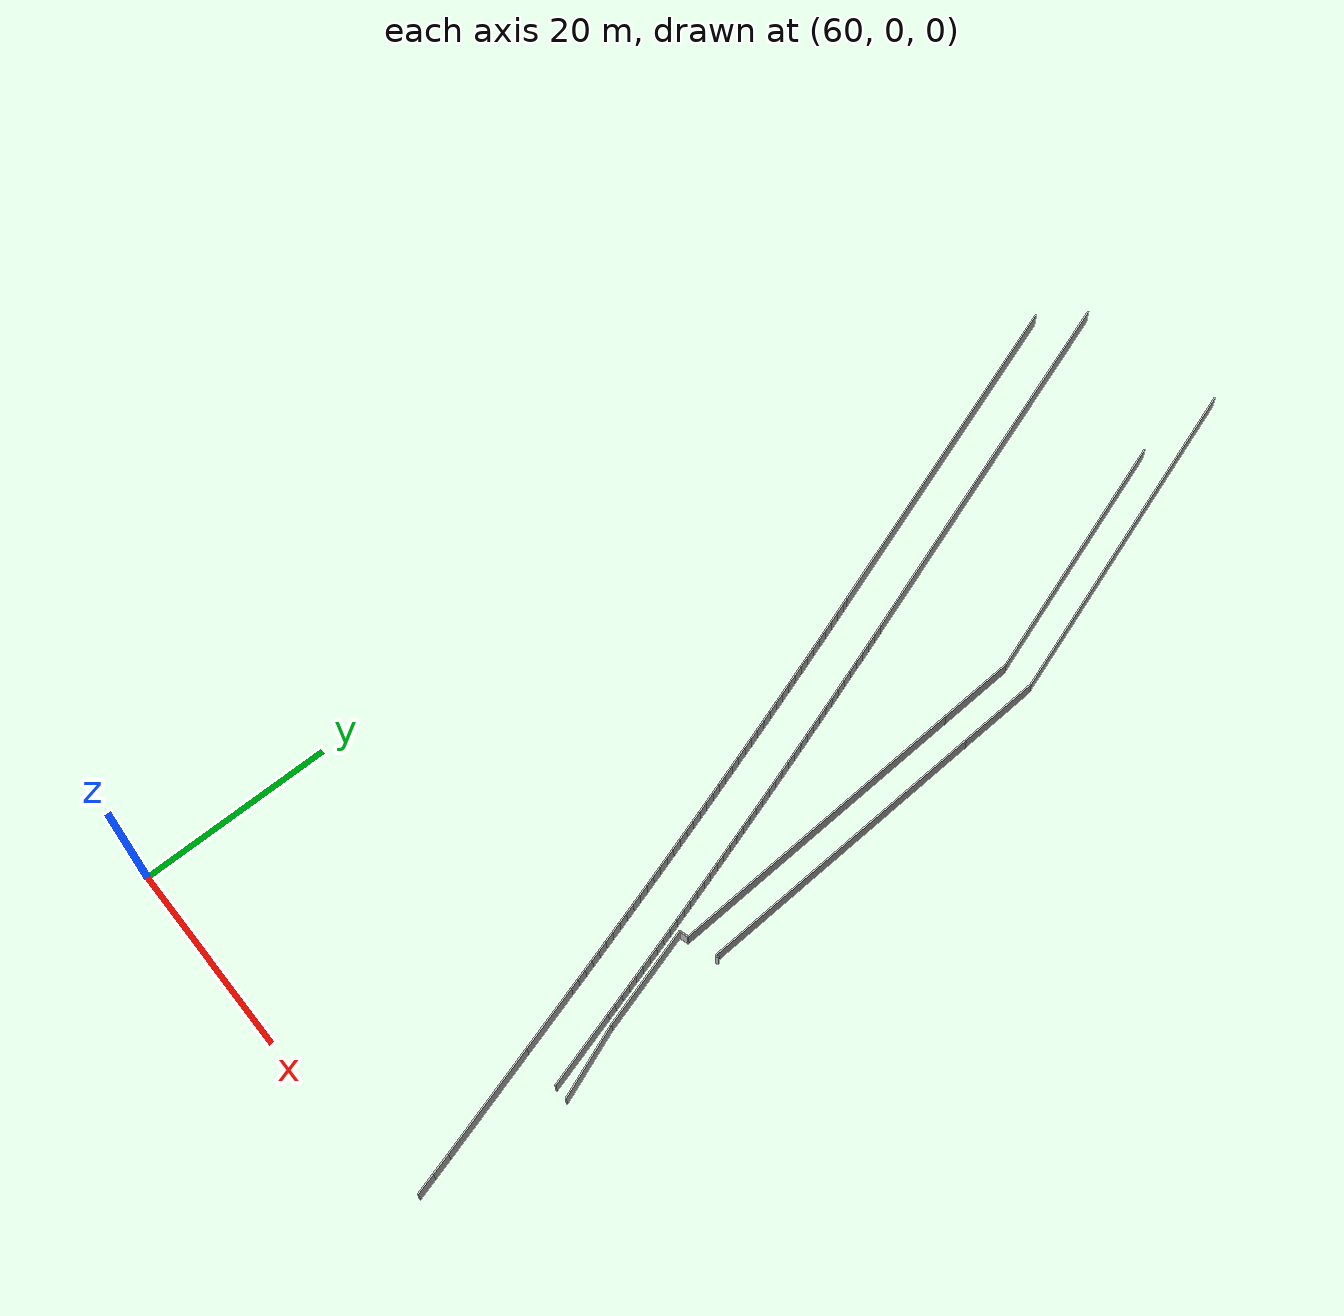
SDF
<?xml version="1.0" ?>
<sdf version="1.6">
  <model name="sps_2215">
    <pose frame="">0 0 0 0 -0 0</pose>
    <static>1</static>
    <self_collide>0</self_collide>
    <allow_auto_disable>0</allow_auto_disable>
    <link name="Wall79">
      <kinematic>0</kinematic>
      <gravity>1</gravity>
      <self_collide>0</self_collide>
      <collision name="collision">
        <geometry>
          <box>
            <size>34.9065 0.15 2.5</size>
          </box>
        </geometry>
        <pose frame="">0 0 0 0 -0 0</pose>
      </collision>
      <visual name="visual">
        <geometry>
          <box>
            <size>34.9065 0.15 2.5</size>
          </box>
        </geometry>
        <pose frame="">0 0 0 0 -0 0</pose>
        <cast_shadows>1</cast_shadows>
        <transparency>0.0</transparency>
      </visual>
      <pose frame="">90.3598 92.6503 1.25 0 0 -1.22655</pose>
    </link>
    <link name="Wall153">
      <kinematic>0</kinematic>
      <gravity>1</gravity>
      <self_collide>0</self_collide>
      <collision name="collision">
        <geometry>
          <box>
            <size>0.94426 0.15 2.5</size>
          </box>
        </geometry>
        <pose frame="">0 0 0 0 -0 0</pose>
      </collision>
      <visual name="visual">
        <geometry>
          <box>
            <size>0.94426 0.15 2.5</size>
          </box>
        </geometry>
        <pose frame="">0 0 0 0 -0 0</pose>
        <cast_shadows>1</cast_shadows>
        <transparency>0.0</transparency>
      </visual>
      <pose frame="">95.4233 35.6831 1.25 0 -0 0.298855</pose>
    </link>
    <link name="Wall154">
      <kinematic>0</kinematic>
      <gravity>1</gravity>
      <self_collide>0</self_collide>
      <collision name="collision">
        <geometry>
          <box>
            <size>11.8573 0.15 2.5</size>
          </box>
        </geometry>
        <pose frame="">0 0 0 0 -0 0</pose>
      </collision>
      <visual name="visual">
        <geometry>
          <box>
            <size>11.8573 0.15 2.5</size>
          </box>
        </geometry>
        <pose frame="">0 0 0 0 -0 0</pose>
        <cast_shadows>1</cast_shadows>
        <transparency>0.0</transparency>
      </visual>
      <pose frame="">96.9025 12.2199 1.25 0 -0 1.86542</pose>
    </link>
    <link name="Wall155">
      <kinematic>0</kinematic>
      <gravity>1</gravity>
      <self_collide>0</self_collide>
      <collision name="collision">
        <geometry>
          <box>
            <size>6.81214 0.15 2.5</size>
          </box>
        </geometry>
        <pose frame="">0 0 0 0 -0 0</pose>
      </collision>
      <visual name="visual">
        <geometry>
          <box>
            <size>6.81214 0.15 2.5</size>
          </box>
        </geometry>
        <pose frame="">0 0 0 0 -0 0</pose>
        <cast_shadows>1</cast_shadows>
        <transparency>0.0</transparency>
      </visual>
      <pose frame="">94.1919 21.1524 1.25 0 -0 1.86542</pose>
    </link>
    <link name="Wall259">
      <kinematic>0</kinematic>
      <gravity>1</gravity>
      <self_collide>0</self_collide>
      <collision name="collision">
        <geometry>
          <box>
            <size>10.7821 0.15 2.5</size>
          </box>
        </geometry>
        <pose frame="">0 0 0 0 -0 0</pose>
      </collision>
      <visual name="visual">
        <geometry>
          <box>
            <size>10.7821 0.15 2.5</size>
          </box>
        </geometry>
        <pose frame="">0 0 0 0 -0 0</pose>
        <cast_shadows>1</cast_shadows>
        <transparency>0.0</transparency>
      </visual>
      <pose frame="">96.557 30.3913 1.25 0 0 -1.2724</pose>
    </link>
    <link name="Wall321">
      <kinematic>0</kinematic>
      <gravity>1</gravity>
      <self_collide>0</self_collide>
      <collision name="collision">
        <geometry>
          <box>
            <size>38.8428 0.15 2.5</size>
          </box>
        </geometry>
        <pose frame="">0 0 0 0 -0 0</pose>
      </collision>
      <visual name="visual">
        <geometry>
          <box>
            <size>38.8428 0.15 2.5</size>
          </box>
        </geometry>
        <pose frame="">0 0 0 0 -0 0</pose>
        <cast_shadows>1</cast_shadows>
        <transparency>0.0</transparency>
      </visual>
      <pose frame="">76.4372 87.007 1.25 0 0 -1.22664</pose>
    </link>
    <link name="Wall578">
      <kinematic>0</kinematic>
      <gravity>1</gravity>
      <self_collide>0</self_collide>
      <collision name="collision">
        <geometry>
          <box>
            <size>26.1171 0.15 2.5</size>
          </box>
        </geometry>
        <pose frame="">0 0 0 0 -0 0</pose>
      </collision>
      <visual name="visual">
        <geometry>
          <box>
            <size>26.1171 0.15 2.5</size>
          </box>
        </geometry>
        <pose frame="">0 0 0 0 -0 0</pose>
        <cast_shadows>1</cast_shadows>
        <transparency>0.0</transparency>
      </visual>
      <pose frame="">88.8765 87.8979 1.25 0 0 -1.22655</pose>
    </link>
    <link name="Wall579">
      <kinematic>0</kinematic>
      <gravity>1</gravity>
      <self_collide>0</self_collide>
      <collision name="collision">
        <geometry>
          <box>
            <size>8.34564 0.15 2.5</size>
          </box>
        </geometry>
        <pose frame="">0 0 0 0 -0 0</pose>
      </collision>
      <visual name="visual">
        <geometry>
          <box>
            <size>8.34564 0.15 2.5</size>
          </box>
        </geometry>
        <pose frame="">0 0 0 0 -0 0</pose>
        <cast_shadows>1</cast_shadows>
        <transparency>0.0</transparency>
      </visual>
      <pose frame="">96.5213 72.0571 1.25 0 0 -1.50576</pose>
    </link>
    <link name="Wall580">
      <kinematic>0</kinematic>
      <gravity>1</gravity>
      <self_collide>0</self_collide>
      <collision name="collision">
        <geometry>
          <box>
            <size>31.2306 0.15 2.5</size>
          </box>
        </geometry>
        <pose frame="">0 0 0 0 -0 0</pose>
      </collision>
      <visual name="visual">
        <geometry>
          <box>
            <size>31.2306 0.15 2.5</size>
          </box>
        </geometry>
        <pose frame="">0 0 0 0 -0 0</pose>
        <cast_shadows>1</cast_shadows>
        <transparency>0.0</transparency>
      </visual>
      <pose frame="">97.8072 52.3108 1.25 0 0 -1.50576</pose>
    </link>
    <link name="Wall581">
      <kinematic>0</kinematic>
      <gravity>1</gravity>
      <self_collide>0</self_collide>
      <collision name="collision">
        <geometry>
          <box>
            <size>0.371875 0.15 2.5</size>
          </box>
        </geometry>
        <pose frame="">0 0 0 0 -0 0</pose>
      </collision>
      <visual name="visual">
        <geometry>
          <box>
            <size>0.371875 0.15 2.5</size>
          </box>
        </geometry>
        <pose frame="">0 0 0 0 -0 0</pose>
        <cast_shadows>1</cast_shadows>
        <transparency>0.0</transparency>
      </visual>
      <pose frame="">98.9997 36.7832 1.25 0 -0 0.298704</pose>
    </link>
    <link name="Wall582">
      <kinematic>0</kinematic>
      <gravity>1</gravity>
      <self_collide>0</self_collide>
      <collision name="collision">
        <geometry>
          <box>
            <size>8.06476 0.15 2.5</size>
          </box>
        </geometry>
        <pose frame="">0 0 0 0 -0 0</pose>
      </collision>
      <visual name="visual">
        <geometry>
          <box>
            <size>8.06476 0.15 2.5</size>
          </box>
        </geometry>
        <pose frame="">0 0 0 0 -0 0</pose>
        <cast_shadows>1</cast_shadows>
        <transparency>0.0</transparency>
      </visual>
      <pose frame="">98.3365 21.7518 1.25 0 0 -1.27624</pose>
    </link>
    <link name="Wall656">
      <kinematic>0</kinematic>
      <gravity>1</gravity>
      <self_collide>0</self_collide>
      <collision name="collision">
        <geometry>
          <box>
            <size>0.58996 0.15 2.5</size>
          </box>
        </geometry>
        <pose frame="">0 0 0 0 -0 0</pose>
      </collision>
      <visual name="visual">
        <geometry>
          <box>
            <size>0.58996 0.15 2.5</size>
          </box>
        </geometry>
        <pose frame="">0 0 0 0 -0 0</pose>
        <cast_shadows>1</cast_shadows>
        <transparency>0.0</transparency>
      </visual>
      <pose frame="">78.9899 67.6154 1.25 0 -0 1.91499</pose>
    </link>
    <link name="Wall657">
      <kinematic>0</kinematic>
      <gravity>1</gravity>
      <self_collide>0</self_collide>
      <collision name="collision">
        <geometry>
          <box>
            <size>35.1918 0.15 2.5</size>
          </box>
        </geometry>
        <pose frame="">0 0 0 0 -0 0</pose>
      </collision>
      <visual name="visual">
        <geometry>
          <box>
            <size>35.1918 0.15 2.5</size>
          </box>
        </geometry>
        <pose frame="">0 0 0 0 -0 0</pose>
        <cast_shadows>1</cast_shadows>
        <transparency>0.0</transparency>
      </visual>
      <pose frame="">72.9529 84.457 1.25 0 -0 1.91499</pose>
    </link>
    <link name="Wall658">
      <kinematic>0</kinematic>
      <gravity>1</gravity>
      <self_collide>0</self_collide>
      <collision name="collision">
        <geometry>
          <box>
            <size>7.72874 0.15 2.5</size>
          </box>
        </geometry>
        <pose frame="">0 0 0 0 -0 0</pose>
      </collision>
      <visual name="visual">
        <geometry>
          <box>
            <size>7.72874 0.15 2.5</size>
          </box>
        </geometry>
        <pose frame="">0 0 0 0 -0 0</pose>
        <cast_shadows>1</cast_shadows>
        <transparency>0.0</transparency>
      </visual>
      <pose frame="">93.5348 71.7493 1.25 0 0 -1.50576</pose>
    </link>
    <link name="Wall659">
      <kinematic>0</kinematic>
      <gravity>1</gravity>
      <self_collide>0</self_collide>
      <collision name="collision">
        <geometry>
          <box>
            <size>32.1389 0.15 2.5</size>
          </box>
        </geometry>
        <pose frame="">0 0 0 0 -0 0</pose>
      </collision>
      <visual name="visual">
        <geometry>
          <box>
            <size>32.1389 0.15 2.5</size>
          </box>
        </geometry>
        <pose frame="">0 0 0 0 -0 0</pose>
        <cast_shadows>1</cast_shadows>
        <transparency>0.0</transparency>
      </visual>
      <pose frame="">94.8302 51.8576 1.25 0 0 -1.50576</pose>
    </link>
    <link name="Wall661">
      <kinematic>0</kinematic>
      <gravity>1</gravity>
      <self_collide>0</self_collide>
      <collision name="collision">
        <geometry>
          <box>
            <size>7.90182 0.15 2.5</size>
          </box>
        </geometry>
        <pose frame="">0 0 0 0 -0 0</pose>
      </collision>
      <visual name="visual">
        <geometry>
          <box>
            <size>7.90182 0.15 2.5</size>
          </box>
        </geometry>
        <pose frame="">0 0 0 0 -0 0</pose>
        <cast_shadows>1</cast_shadows>
        <transparency>0.0</transparency>
      </visual>
      <pose frame="">99.5982 21.5658 1.25 0 0 -1.19328</pose>
    </link>
    <link name="Wall6433">
      <kinematic>0</kinematic>
      <gravity>1</gravity>
      <self_collide>0</self_collide>
      <collision name="collision">
        <geometry>
          <box>
            <size>2.24457 0.15 2.5</size>
          </box>
        </geometry>
        <pose frame="">0 0 0 0 -0 0</pose>
      </collision>
      <visual name="visual">
        <geometry>
          <box>
            <size>2.24457 0.15 2.5</size>
          </box>
        </geometry>
        <pose frame="">0 0 0 0 -0 0</pose>
        <cast_shadows>1</cast_shadows>
        <transparency>0.0</transparency>
      </visual>
      <pose frame="">99.5833 3.31898 1.25 0 -0 1.85808</pose>
    </link>
    <link name="Wall6434">
      <kinematic>0</kinematic>
      <gravity>1</gravity>
      <self_collide>0</self_collide>
      <collision name="collision">
        <geometry>
          <box>
            <size>2.24496 0.15 2.5</size>
          </box>
        </geometry>
        <pose frame="">0 0 0 0 -0 0</pose>
      </collision>
      <visual name="visual">
        <geometry>
          <box>
            <size>2.24496 0.15 2.5</size>
          </box>
        </geometry>
        <pose frame="">0 0 0 0 -0 0</pose>
        <cast_shadows>1</cast_shadows>
        <transparency>0.0</transparency>
      </visual>
      <pose frame="">98.9447 5.47099 1.25 0 -0 1.86046</pose>
    </link>
    <link name="Wall8240">
      <kinematic>0</kinematic>
      <gravity>1</gravity>
      <self_collide>0</self_collide>
      <collision name="collision">
        <geometry>
          <box>
            <size>1.08068 0.15 2.5</size>
          </box>
        </geometry>
        <pose frame="">0 0 0 0 -0 0</pose>
      </collision>
      <visual name="visual">
        <geometry>
          <box>
            <size>1.08068 0.15 2.5</size>
          </box>
        </geometry>
        <pose frame="">0 0 0 0 -0 0</pose>
        <cast_shadows>1</cast_shadows>
        <transparency>0.0</transparency>
      </visual>
      <pose frame="">97.0091 26.1276 1.25 0 -0 1.86522</pose>
    </link>
    <link name="Wall8241">
      <kinematic>0</kinematic>
      <gravity>1</gravity>
      <self_collide>0</self_collide>
      <collision name="collision">
        <geometry>
          <box>
            <size>1.08069 0.15 2.5</size>
          </box>
        </geometry>
        <pose frame="">0 0 0 0 -0 0</pose>
      </collision>
      <visual name="visual">
        <geometry>
          <box>
            <size>1.08069 0.15 2.5</size>
          </box>
        </geometry>
        <pose frame="">0 0 0 0 -0 0</pose>
        <cast_shadows>1</cast_shadows>
        <transparency>0.0</transparency>
      </visual>
      <pose frame="">96.6948 27.1616 1.25 0 -0 1.8664</pose>
    </link>
    <link name="Wall8242">
      <kinematic>0</kinematic>
      <gravity>1</gravity>
      <self_collide>0</self_collide>
      <collision name="collision">
        <geometry>
          <box>
            <size>1.08062 0.15 2.5</size>
          </box>
        </geometry>
        <pose frame="">0 0 0 0 -0 0</pose>
      </collision>
      <visual name="visual">
        <geometry>
          <box>
            <size>1.08062 0.15 2.5</size>
          </box>
        </geometry>
        <pose frame="">0 0 0 0 -0 0</pose>
        <cast_shadows>1</cast_shadows>
        <transparency>0.0</transparency>
      </visual>
      <pose frame="">96.3794 28.1952 1.25 0 -0 1.86754</pose>
    </link>
    <link name="Wall8243">
      <kinematic>0</kinematic>
      <gravity>1</gravity>
      <self_collide>0</self_collide>
      <collision name="collision">
        <geometry>
          <box>
            <size>1.08074 0.15 2.5</size>
          </box>
        </geometry>
        <pose frame="">0 0 0 0 -0 0</pose>
      </collision>
      <visual name="visual">
        <geometry>
          <box>
            <size>1.08074 0.15 2.5</size>
          </box>
        </geometry>
        <pose frame="">0 0 0 0 -0 0</pose>
        <cast_shadows>1</cast_shadows>
        <transparency>0.0</transparency>
      </visual>
      <pose frame="">96.0629 29.2285 1.25 0 -0 1.86851</pose>
    </link>
    <link name="Wall8244">
      <kinematic>0</kinematic>
      <gravity>1</gravity>
      <self_collide>0</self_collide>
      <collision name="collision">
        <geometry>
          <box>
            <size>1.08074 0.15 2.5</size>
          </box>
        </geometry>
        <pose frame="">0 0 0 0 -0 0</pose>
      </collision>
      <visual name="visual">
        <geometry>
          <box>
            <size>1.08074 0.15 2.5</size>
          </box>
        </geometry>
        <pose frame="">0 0 0 0 -0 0</pose>
        <cast_shadows>1</cast_shadows>
        <transparency>0.0</transparency>
      </visual>
      <pose frame="">95.7454 30.2615 1.25 0 -0 1.86963</pose>
    </link>
    <link name="Wall8245">
      <kinematic>0</kinematic>
      <gravity>1</gravity>
      <self_collide>0</self_collide>
      <collision name="collision">
        <geometry>
          <box>
            <size>1.08063 0.15 2.5</size>
          </box>
        </geometry>
        <pose frame="">0 0 0 0 -0 0</pose>
      </collision>
      <visual name="visual">
        <geometry>
          <box>
            <size>1.08063 0.15 2.5</size>
          </box>
        </geometry>
        <pose frame="">0 0 0 0 -0 0</pose>
        <cast_shadows>1</cast_shadows>
        <transparency>0.0</transparency>
      </visual>
      <pose frame="">95.4267 31.2941 1.25 0 -0 1.87067</pose>
    </link>
    <link name="Wall8246">
      <kinematic>0</kinematic>
      <gravity>1</gravity>
      <self_collide>0</self_collide>
      <collision name="collision">
        <geometry>
          <box>
            <size>1.08064 0.15 2.5</size>
          </box>
        </geometry>
        <pose frame="">0 0 0 0 -0 0</pose>
      </collision>
      <visual name="visual">
        <geometry>
          <box>
            <size>1.08064 0.15 2.5</size>
          </box>
        </geometry>
        <pose frame="">0 0 0 0 -0 0</pose>
        <cast_shadows>1</cast_shadows>
        <transparency>0.0</transparency>
      </visual>
      <pose frame="">95.1067 32.3263 1.25 0 -0 1.87202</pose>
    </link>
    <link name="Wall8247">
      <kinematic>0</kinematic>
      <gravity>1</gravity>
      <self_collide>0</self_collide>
      <collision name="collision">
        <geometry>
          <box>
            <size>1.08076 0.15 2.5</size>
          </box>
        </geometry>
        <pose frame="">0 0 0 0 -0 0</pose>
      </collision>
      <visual name="visual">
        <geometry>
          <box>
            <size>1.08076 0.15 2.5</size>
          </box>
        </geometry>
        <pose frame="">0 0 0 0 -0 0</pose>
        <cast_shadows>1</cast_shadows>
        <transparency>0.0</transparency>
      </visual>
      <pose frame="">94.7856 33.3582 1.25 0 -0 1.87294</pose>
    </link>
    <link name="Wall8248">
      <kinematic>0</kinematic>
      <gravity>1</gravity>
      <self_collide>0</self_collide>
      <collision name="collision">
        <geometry>
          <box>
            <size>1.08077 0.15 2.5</size>
          </box>
        </geometry>
        <pose frame="">0 0 0 0 -0 0</pose>
      </collision>
      <visual name="visual">
        <geometry>
          <box>
            <size>1.08077 0.15 2.5</size>
          </box>
        </geometry>
        <pose frame="">0 0 0 0 -0 0</pose>
        <cast_shadows>1</cast_shadows>
        <transparency>0.0</transparency>
      </visual>
      <pose frame="">94.4633 34.3898 1.25 0 -0 1.87429</pose>
    </link>
    <link name="Wall8249">
      <kinematic>0</kinematic>
      <gravity>1</gravity>
      <self_collide>0</self_collide>
      <collision name="collision">
        <geometry>
          <box>
            <size>1.08071 0.15 2.5</size>
          </box>
        </geometry>
        <pose frame="">0 0 0 0 -0 0</pose>
      </collision>
      <visual name="visual">
        <geometry>
          <box>
            <size>1.08071 0.15 2.5</size>
          </box>
        </geometry>
        <pose frame="">0 0 0 0 -0 0</pose>
        <cast_shadows>1</cast_shadows>
        <transparency>0.0</transparency>
      </visual>
      <pose frame="">94.1399 35.421 1.25 0 -0 1.87526</pose>
    </link>
    <link name="Wall8250">
      <kinematic>0</kinematic>
      <gravity>1</gravity>
      <self_collide>0</self_collide>
      <collision name="collision">
        <geometry>
          <box>
            <size>1.08073 0.15 2.5</size>
          </box>
        </geometry>
        <pose frame="">0 0 0 0 -0 0</pose>
      </collision>
      <visual name="visual">
        <geometry>
          <box>
            <size>1.08073 0.15 2.5</size>
          </box>
        </geometry>
        <pose frame="">0 0 0 0 -0 0</pose>
        <cast_shadows>1</cast_shadows>
        <transparency>0.0</transparency>
      </visual>
      <pose frame="">93.8153 36.4518 1.25 0 -0 1.87644</pose>
    </link>
    <link name="Wall8251">
      <kinematic>0</kinematic>
      <gravity>1</gravity>
      <self_collide>0</self_collide>
      <collision name="collision">
        <geometry>
          <box>
            <size>1.08063 0.15 2.5</size>
          </box>
        </geometry>
        <pose frame="">0 0 0 0 -0 0</pose>
      </collision>
      <visual name="visual">
        <geometry>
          <box>
            <size>1.08063 0.15 2.5</size>
          </box>
        </geometry>
        <pose frame="">0 0 0 0 -0 0</pose>
        <cast_shadows>1</cast_shadows>
        <transparency>0.0</transparency>
      </visual>
      <pose frame="">93.4895 37.4822 1.25 0 -0 1.87765</pose>
    </link>
    <link name="Wall8252">
      <kinematic>0</kinematic>
      <gravity>1</gravity>
      <self_collide>0</self_collide>
      <collision name="collision">
        <geometry>
          <box>
            <size>1.08069 0.15 2.5</size>
          </box>
        </geometry>
        <pose frame="">0 0 0 0 -0 0</pose>
      </collision>
      <visual name="visual">
        <geometry>
          <box>
            <size>1.08069 0.15 2.5</size>
          </box>
        </geometry>
        <pose frame="">0 0 0 0 -0 0</pose>
        <cast_shadows>1</cast_shadows>
        <transparency>0.0</transparency>
      </visual>
      <pose frame="">93.1625 38.5122 1.25 0 -0 1.87876</pose>
    </link>
    <link name="Wall8253">
      <kinematic>0</kinematic>
      <gravity>1</gravity>
      <self_collide>0</self_collide>
      <collision name="collision">
        <geometry>
          <box>
            <size>1.08083 0.15 2.5</size>
          </box>
        </geometry>
        <pose frame="">0 0 0 0 -0 0</pose>
      </collision>
      <visual name="visual">
        <geometry>
          <box>
            <size>1.08083 0.15 2.5</size>
          </box>
        </geometry>
        <pose frame="">0 0 0 0 -0 0</pose>
        <cast_shadows>1</cast_shadows>
        <transparency>0.0</transparency>
      </visual>
      <pose frame="">92.8343 39.5419 1.25 0 -0 1.8799</pose>
    </link>
    <link name="Wall8254">
      <kinematic>0</kinematic>
      <gravity>1</gravity>
      <self_collide>0</self_collide>
      <collision name="collision">
        <geometry>
          <box>
            <size>1.08079 0.15 2.5</size>
          </box>
        </geometry>
        <pose frame="">0 0 0 0 -0 0</pose>
      </collision>
      <visual name="visual">
        <geometry>
          <box>
            <size>1.08079 0.15 2.5</size>
          </box>
        </geometry>
        <pose frame="">0 0 0 0 -0 0</pose>
        <cast_shadows>1</cast_shadows>
        <transparency>0.0</transparency>
      </visual>
      <pose frame="">92.5049 40.5713 1.25 0 -0 1.8811</pose>
    </link>
    <link name="Wall8255">
      <kinematic>0</kinematic>
      <gravity>1</gravity>
      <self_collide>0</self_collide>
      <collision name="collision">
        <geometry>
          <box>
            <size>1.08057 0.15 2.5</size>
          </box>
        </geometry>
        <pose frame="">0 0 0 0 -0 0</pose>
      </collision>
      <visual name="visual">
        <geometry>
          <box>
            <size>1.08057 0.15 2.5</size>
          </box>
        </geometry>
        <pose frame="">0 0 0 0 -0 0</pose>
        <cast_shadows>1</cast_shadows>
        <transparency>0.0</transparency>
      </visual>
      <pose frame="">92.1744 41.6002 1.25 0 -0 1.88212</pose>
    </link>
    <link name="Wall8256">
      <kinematic>0</kinematic>
      <gravity>1</gravity>
      <self_collide>0</self_collide>
      <collision name="collision">
        <geometry>
          <box>
            <size>1.08077 0.15 2.5</size>
          </box>
        </geometry>
        <pose frame="">0 0 0 0 -0 0</pose>
      </collision>
      <visual name="visual">
        <geometry>
          <box>
            <size>1.08077 0.15 2.5</size>
          </box>
        </geometry>
        <pose frame="">0 0 0 0 -0 0</pose>
        <cast_shadows>1</cast_shadows>
        <transparency>0.0</transparency>
      </visual>
      <pose frame="">91.8427 42.6287 1.25 0 -0 1.88342</pose>
    </link>
    <link name="Wall8257">
      <kinematic>0</kinematic>
      <gravity>1</gravity>
      <self_collide>0</self_collide>
      <collision name="collision">
        <geometry>
          <box>
            <size>1.08051 0.15 2.5</size>
          </box>
        </geometry>
        <pose frame="">0 0 0 0 -0 0</pose>
      </collision>
      <visual name="visual">
        <geometry>
          <box>
            <size>1.08051 0.15 2.5</size>
          </box>
        </geometry>
        <pose frame="">0 0 0 0 -0 0</pose>
        <cast_shadows>1</cast_shadows>
        <transparency>0.0</transparency>
      </visual>
      <pose frame="">91.5098 43.6568 1.25 0 -0 1.88451</pose>
    </link>
    <link name="Wall8258">
      <kinematic>0</kinematic>
      <gravity>1</gravity>
      <self_collide>0</self_collide>
      <collision name="collision">
        <geometry>
          <box>
            <size>1.08075 0.15 2.5</size>
          </box>
        </geometry>
        <pose frame="">0 0 0 0 -0 0</pose>
      </collision>
      <visual name="visual">
        <geometry>
          <box>
            <size>1.08075 0.15 2.5</size>
          </box>
        </geometry>
        <pose frame="">0 0 0 0 -0 0</pose>
        <cast_shadows>1</cast_shadows>
        <transparency>0.0</transparency>
      </visual>
      <pose frame="">91.1757 44.6845 1.25 0 -0 1.88556</pose>
    </link>
    <link name="Wall8259">
      <kinematic>0</kinematic>
      <gravity>1</gravity>
      <self_collide>0</self_collide>
      <collision name="collision">
        <geometry>
          <box>
            <size>1.08066 0.15 2.5</size>
          </box>
        </geometry>
        <pose frame="">0 0 0 0 -0 0</pose>
      </collision>
      <visual name="visual">
        <geometry>
          <box>
            <size>1.08066 0.15 2.5</size>
          </box>
        </geometry>
        <pose frame="">0 0 0 0 -0 0</pose>
        <cast_shadows>1</cast_shadows>
        <transparency>0.0</transparency>
      </visual>
      <pose frame="">90.8405 45.7119 1.25 0 -0 1.88678</pose>
    </link>
    <link name="Wall8260">
      <kinematic>0</kinematic>
      <gravity>1</gravity>
      <self_collide>0</self_collide>
      <collision name="collision">
        <geometry>
          <box>
            <size>1.08062 0.15 2.5</size>
          </box>
        </geometry>
        <pose frame="">0 0 0 0 -0 0</pose>
      </collision>
      <visual name="visual">
        <geometry>
          <box>
            <size>1.08062 0.15 2.5</size>
          </box>
        </geometry>
        <pose frame="">0 0 0 0 -0 0</pose>
        <cast_shadows>1</cast_shadows>
        <transparency>0.0</transparency>
      </visual>
      <pose frame="">90.5042 46.7389 1.25 0 -0 1.88774</pose>
    </link>
    <link name="Wall8261">
      <kinematic>0</kinematic>
      <gravity>1</gravity>
      <self_collide>0</self_collide>
      <collision name="collision">
        <geometry>
          <box>
            <size>1.08088 0.15 2.5</size>
          </box>
        </geometry>
        <pose frame="">0 0 0 0 -0 0</pose>
      </collision>
      <visual name="visual">
        <geometry>
          <box>
            <size>1.08088 0.15 2.5</size>
          </box>
        </geometry>
        <pose frame="">0 0 0 0 -0 0</pose>
        <cast_shadows>1</cast_shadows>
        <transparency>0.0</transparency>
      </visual>
      <pose frame="">90.1667 47.7656 1.25 0 -0 1.88903</pose>
    </link>
    <link name="Wall8262">
      <kinematic>0</kinematic>
      <gravity>1</gravity>
      <self_collide>0</self_collide>
      <collision name="collision">
        <geometry>
          <box>
            <size>1.08051 0.15 2.5</size>
          </box>
        </geometry>
        <pose frame="">0 0 0 0 -0 0</pose>
      </collision>
      <visual name="visual">
        <geometry>
          <box>
            <size>1.08051 0.15 2.5</size>
          </box>
        </geometry>
        <pose frame="">0 0 0 0 -0 0</pose>
        <cast_shadows>1</cast_shadows>
        <transparency>0.0</transparency>
      </visual>
      <pose frame="">89.8279 48.7918 1.25 0 -0 1.89033</pose>
    </link>
    <link name="Wall8263">
      <kinematic>0</kinematic>
      <gravity>1</gravity>
      <self_collide>0</self_collide>
      <collision name="collision">
        <geometry>
          <box>
            <size>1.08059 0.15 2.5</size>
          </box>
        </geometry>
        <pose frame="">0 0 0 0 -0 0</pose>
      </collision>
      <visual name="visual">
        <geometry>
          <box>
            <size>1.08059 0.15 2.5</size>
          </box>
        </geometry>
        <pose frame="">0 0 0 0 -0 0</pose>
        <cast_shadows>1</cast_shadows>
        <transparency>0.0</transparency>
      </visual>
      <pose frame="">89.488 49.8175 1.25 0 -0 1.89126</pose>
    </link>
    <link name="Wall8264">
      <kinematic>0</kinematic>
      <gravity>1</gravity>
      <self_collide>0</self_collide>
      <collision name="collision">
        <geometry>
          <box>
            <size>1.08068 0.15 2.5</size>
          </box>
        </geometry>
        <pose frame="">0 0 0 0 -0 0</pose>
      </collision>
      <visual name="visual">
        <geometry>
          <box>
            <size>1.08068 0.15 2.5</size>
          </box>
        </geometry>
        <pose frame="">0 0 0 0 -0 0</pose>
        <cast_shadows>1</cast_shadows>
        <transparency>0.0</transparency>
      </visual>
      <pose frame="">89.1469 50.8429 1.25 0 -0 1.8926</pose>
    </link>
    <link name="Wall8265">
      <kinematic>0</kinematic>
      <gravity>1</gravity>
      <self_collide>0</self_collide>
      <collision name="collision">
        <geometry>
          <box>
            <size>1.08059 0.15 2.5</size>
          </box>
        </geometry>
        <pose frame="">0 0 0 0 -0 0</pose>
      </collision>
      <visual name="visual">
        <geometry>
          <box>
            <size>1.08059 0.15 2.5</size>
          </box>
        </geometry>
        <pose frame="">0 0 0 0 -0 0</pose>
        <cast_shadows>1</cast_shadows>
        <transparency>0.0</transparency>
      </visual>
      <pose frame="">88.8046 51.8679 1.25 0 -0 1.89358</pose>
    </link>
    <link name="Wall8266">
      <kinematic>0</kinematic>
      <gravity>1</gravity>
      <self_collide>0</self_collide>
      <collision name="collision">
        <geometry>
          <box>
            <size>1.08063 0.15 2.5</size>
          </box>
        </geometry>
        <pose frame="">0 0 0 0 -0 0</pose>
      </collision>
      <visual name="visual">
        <geometry>
          <box>
            <size>1.08063 0.15 2.5</size>
          </box>
        </geometry>
        <pose frame="">0 0 0 0 -0 0</pose>
        <cast_shadows>1</cast_shadows>
        <transparency>0.0</transparency>
      </visual>
      <pose frame="">88.4613 52.8925 1.25 0 -0 1.89476</pose>
    </link>
    <link name="Wall8267">
      <kinematic>0</kinematic>
      <gravity>1</gravity>
      <self_collide>0</self_collide>
      <collision name="collision">
        <geometry>
          <box>
            <size>1.08084 0.15 2.5</size>
          </box>
        </geometry>
        <pose frame="">0 0 0 0 -0 0</pose>
      </collision>
      <visual name="visual">
        <geometry>
          <box>
            <size>1.08084 0.15 2.5</size>
          </box>
        </geometry>
        <pose frame="">0 0 0 0 -0 0</pose>
        <cast_shadows>1</cast_shadows>
        <transparency>0.0</transparency>
      </visual>
      <pose frame="">88.1167 53.9168 1.25 0 -0 1.89589</pose>
    </link>
    <link name="Wall8268">
      <kinematic>0</kinematic>
      <gravity>1</gravity>
      <self_collide>0</self_collide>
      <collision name="collision">
        <geometry>
          <box>
            <size>1.08052 0.15 2.5</size>
          </box>
        </geometry>
        <pose frame="">0 0 0 0 -0 0</pose>
      </collision>
      <visual name="visual">
        <geometry>
          <box>
            <size>1.08052 0.15 2.5</size>
          </box>
        </geometry>
        <pose frame="">0 0 0 0 -0 0</pose>
        <cast_shadows>1</cast_shadows>
        <transparency>0.0</transparency>
      </visual>
      <pose frame="">87.771 54.9407 1.25 0 -0 1.89694</pose>
    </link>
    <link name="Wall8269">
      <kinematic>0</kinematic>
      <gravity>1</gravity>
      <self_collide>0</self_collide>
      <collision name="collision">
        <geometry>
          <box>
            <size>1.0808 0.15 2.5</size>
          </box>
        </geometry>
        <pose frame="">0 0 0 0 -0 0</pose>
      </collision>
      <visual name="visual">
        <geometry>
          <box>
            <size>1.0808 0.15 2.5</size>
          </box>
        </geometry>
        <pose frame="">0 0 0 0 -0 0</pose>
        <cast_shadows>1</cast_shadows>
        <transparency>0.0</transparency>
      </visual>
      <pose frame="">87.4242 55.9642 1.25 0 -0 1.89805</pose>
    </link>
    <link name="Wall8270">
      <kinematic>0</kinematic>
      <gravity>1</gravity>
      <self_collide>0</self_collide>
      <collision name="collision">
        <geometry>
          <box>
            <size>1.08076 0.15 2.5</size>
          </box>
        </geometry>
        <pose frame="">0 0 0 0 -0 0</pose>
      </collision>
      <visual name="visual">
        <geometry>
          <box>
            <size>1.08076 0.15 2.5</size>
          </box>
        </geometry>
        <pose frame="">0 0 0 0 -0 0</pose>
        <cast_shadows>1</cast_shadows>
        <transparency>0.0</transparency>
      </visual>
      <pose frame="">87.0762 56.9874 1.25 0 -0 1.89919</pose>
    </link>
    <link name="Wall8271">
      <kinematic>0</kinematic>
      <gravity>1</gravity>
      <self_collide>0</self_collide>
      <collision name="collision">
        <geometry>
          <box>
            <size>1.08058 0.15 2.5</size>
          </box>
        </geometry>
        <pose frame="">0 0 0 0 -0 0</pose>
      </collision>
      <visual name="visual">
        <geometry>
          <box>
            <size>1.08058 0.15 2.5</size>
          </box>
        </geometry>
        <pose frame="">0 0 0 0 -0 0</pose>
        <cast_shadows>1</cast_shadows>
        <transparency>0.0</transparency>
      </visual>
      <pose frame="">86.727 58.0101 1.25 0 -0 1.90044</pose>
    </link>
    <link name="Wall8272">
      <kinematic>0</kinematic>
      <gravity>1</gravity>
      <self_collide>0</self_collide>
      <collision name="collision">
        <geometry>
          <box>
            <size>1.08075 0.15 2.5</size>
          </box>
        </geometry>
        <pose frame="">0 0 0 0 -0 0</pose>
      </collision>
      <visual name="visual">
        <geometry>
          <box>
            <size>1.08075 0.15 2.5</size>
          </box>
        </geometry>
        <pose frame="">0 0 0 0 -0 0</pose>
        <cast_shadows>1</cast_shadows>
        <transparency>0.0</transparency>
      </visual>
      <pose frame="">86.3766 59.0324 1.25 0 -0 1.90158</pose>
    </link>
    <link name="Wall8273">
      <kinematic>0</kinematic>
      <gravity>1</gravity>
      <self_collide>0</self_collide>
      <collision name="collision">
        <geometry>
          <box>
            <size>1.08085 0.15 2.5</size>
          </box>
        </geometry>
        <pose frame="">0 0 0 0 -0 0</pose>
      </collision>
      <visual name="visual">
        <geometry>
          <box>
            <size>1.08085 0.15 2.5</size>
          </box>
        </geometry>
        <pose frame="">0 0 0 0 -0 0</pose>
        <cast_shadows>1</cast_shadows>
        <transparency>0.0</transparency>
      </visual>
      <pose frame="">86.025 60.0544 1.25 0 -0 1.90274</pose>
    </link>
    <link name="Wall8274">
      <kinematic>0</kinematic>
      <gravity>1</gravity>
      <self_collide>0</self_collide>
      <collision name="collision">
        <geometry>
          <box>
            <size>1.08071 0.15 2.5</size>
          </box>
        </geometry>
        <pose frame="">0 0 0 0 -0 0</pose>
      </collision>
      <visual name="visual">
        <geometry>
          <box>
            <size>1.08071 0.15 2.5</size>
          </box>
        </geometry>
        <pose frame="">0 0 0 0 -0 0</pose>
        <cast_shadows>1</cast_shadows>
        <transparency>0.0</transparency>
      </visual>
      <pose frame="">85.6722 61.076 1.25 0 -0 1.90375</pose>
    </link>
    <link name="Wall8275">
      <kinematic>0</kinematic>
      <gravity>1</gravity>
      <self_collide>0</self_collide>
      <collision name="collision">
        <geometry>
          <box>
            <size>1.08057 0.15 2.5</size>
          </box>
        </geometry>
        <pose frame="">0 0 0 0 -0 0</pose>
      </collision>
      <visual name="visual">
        <geometry>
          <box>
            <size>1.08057 0.15 2.5</size>
          </box>
        </geometry>
        <pose frame="">0 0 0 0 -0 0</pose>
        <cast_shadows>1</cast_shadows>
        <transparency>0.0</transparency>
      </visual>
      <pose frame="">85.3184 62.0971 1.25 0 -0 1.90493</pose>
    </link>
    <link name="Wall8276">
      <kinematic>0</kinematic>
      <gravity>1</gravity>
      <self_collide>0</self_collide>
      <collision name="collision">
        <geometry>
          <box>
            <size>1.0808 0.15 2.5</size>
          </box>
        </geometry>
        <pose frame="">0 0 0 0 -0 0</pose>
      </collision>
      <visual name="visual">
        <geometry>
          <box>
            <size>1.0808 0.15 2.5</size>
          </box>
        </geometry>
        <pose frame="">0 0 0 0 -0 0</pose>
        <cast_shadows>1</cast_shadows>
        <transparency>0.0</transparency>
      </visual>
      <pose frame="">84.9634 63.1178 1.25 0 -0 1.90623</pose>
    </link>
    <link name="Wall8277">
      <kinematic>0</kinematic>
      <gravity>1</gravity>
      <self_collide>0</self_collide>
      <collision name="collision">
        <geometry>
          <box>
            <size>1.08057 0.15 2.5</size>
          </box>
        </geometry>
        <pose frame="">0 0 0 0 -0 0</pose>
      </collision>
      <visual name="visual">
        <geometry>
          <box>
            <size>1.08057 0.15 2.5</size>
          </box>
        </geometry>
        <pose frame="">0 0 0 0 -0 0</pose>
        <cast_shadows>1</cast_shadows>
        <transparency>0.0</transparency>
      </visual>
      <pose frame="">84.6072 64.1381 1.25 0 -0 1.90714</pose>
    </link>
    <link name="Wall8278">
      <kinematic>0</kinematic>
      <gravity>1</gravity>
      <self_collide>0</self_collide>
      <collision name="collision">
        <geometry>
          <box>
            <size>1.08084 0.15 2.5</size>
          </box>
        </geometry>
        <pose frame="">0 0 0 0 -0 0</pose>
      </collision>
      <visual name="visual">
        <geometry>
          <box>
            <size>1.08084 0.15 2.5</size>
          </box>
        </geometry>
        <pose frame="">0 0 0 0 -0 0</pose>
        <cast_shadows>1</cast_shadows>
        <transparency>0.0</transparency>
      </visual>
      <pose frame="">84.2499 65.158 1.25 0 -0 1.90837</pose>
    </link>
    <link name="Wall8279">
      <kinematic>0</kinematic>
      <gravity>1</gravity>
      <self_collide>0</self_collide>
      <collision name="collision">
        <geometry>
          <box>
            <size>1.08055 0.15 2.5</size>
          </box>
        </geometry>
        <pose frame="">0 0 0 0 -0 0</pose>
      </collision>
      <visual name="visual">
        <geometry>
          <box>
            <size>1.08055 0.15 2.5</size>
          </box>
        </geometry>
        <pose frame="">0 0 0 0 -0 0</pose>
        <cast_shadows>1</cast_shadows>
        <transparency>0.0</transparency>
      </visual>
      <pose frame="">83.8914 66.1775 1.25 0 -0 1.90948</pose>
    </link>
    <link name="Wall8280">
      <kinematic>0</kinematic>
      <gravity>1</gravity>
      <self_collide>0</self_collide>
      <collision name="collision">
        <geometry>
          <box>
            <size>1.08078 0.15 2.5</size>
          </box>
        </geometry>
        <pose frame="">0 0 0 0 -0 0</pose>
      </collision>
      <visual name="visual">
        <geometry>
          <box>
            <size>1.08078 0.15 2.5</size>
          </box>
        </geometry>
        <pose frame="">0 0 0 0 -0 0</pose>
        <cast_shadows>1</cast_shadows>
        <transparency>0.0</transparency>
      </visual>
      <pose frame="">83.5318 67.1966 1.25 0 -0 1.9106</pose>
    </link>
    <link name="Wall8281">
      <kinematic>0</kinematic>
      <gravity>1</gravity>
      <self_collide>0</self_collide>
      <collision name="collision">
        <geometry>
          <box>
            <size>1.08071 0.15 2.5</size>
          </box>
        </geometry>
        <pose frame="">0 0 0 0 -0 0</pose>
      </collision>
      <visual name="visual">
        <geometry>
          <box>
            <size>1.08071 0.15 2.5</size>
          </box>
        </geometry>
        <pose frame="">0 0 0 0 -0 0</pose>
        <cast_shadows>1</cast_shadows>
        <transparency>0.0</transparency>
      </visual>
      <pose frame="">83.1709 68.2153 1.25 0 -0 1.91194</pose>
    </link>
    <link name="Wall9151">
      <kinematic>0</kinematic>
      <gravity>1</gravity>
      <self_collide>0</self_collide>
      <collision name="collision">
        <geometry>
          <box>
            <size>1.07602 0.15 2.5</size>
          </box>
        </geometry>
        <pose frame="">0 0 0 0 -0 0</pose>
      </collision>
      <visual name="visual">
        <geometry>
          <box>
            <size>1.07602 0.15 2.5</size>
          </box>
        </geometry>
        <pose frame="">0 0 0 0 -0 0</pose>
        <cast_shadows>1</cast_shadows>
        <transparency>0.0</transparency>
      </visual>
      <pose frame="">93.0468 24.9266 1.25 0 -0 1.86499</pose>
    </link>
    <link name="Wall9152">
      <kinematic>0</kinematic>
      <gravity>1</gravity>
      <self_collide>0</self_collide>
      <collision name="collision">
        <geometry>
          <box>
            <size>1.07606 0.15 2.5</size>
          </box>
        </geometry>
        <pose frame="">0 0 0 0 -0 0</pose>
      </collision>
      <visual name="visual">
        <geometry>
          <box>
            <size>1.07606 0.15 2.5</size>
          </box>
        </geometry>
        <pose frame="">0 0 0 0 -0 0</pose>
        <cast_shadows>1</cast_shadows>
        <transparency>0.0</transparency>
      </visual>
      <pose frame="">92.7342 25.9562 1.25 0 -0 1.86628</pose>
    </link>
    <link name="Wall9153">
      <kinematic>0</kinematic>
      <gravity>1</gravity>
      <self_collide>0</self_collide>
      <collision name="collision">
        <geometry>
          <box>
            <size>1.07595 0.15 2.5</size>
          </box>
        </geometry>
        <pose frame="">0 0 0 0 -0 0</pose>
      </collision>
      <visual name="visual">
        <geometry>
          <box>
            <size>1.07595 0.15 2.5</size>
          </box>
        </geometry>
        <pose frame="">0 0 0 0 -0 0</pose>
        <cast_shadows>1</cast_shadows>
        <transparency>0.0</transparency>
      </visual>
      <pose frame="">92.4203 26.9854 1.25 0 -0 1.86732</pose>
    </link>
    <link name="Wall9154">
      <kinematic>0</kinematic>
      <gravity>1</gravity>
      <self_collide>0</self_collide>
      <collision name="collision">
        <geometry>
          <box>
            <size>1.07596 0.15 2.5</size>
          </box>
        </geometry>
        <pose frame="">0 0 0 0 -0 0</pose>
      </collision>
      <visual name="visual">
        <geometry>
          <box>
            <size>1.07596 0.15 2.5</size>
          </box>
        </geometry>
        <pose frame="">0 0 0 0 -0 0</pose>
        <cast_shadows>1</cast_shadows>
        <transparency>0.0</transparency>
      </visual>
      <pose frame="">92.1053 28.0142 1.25 0 -0 1.86851</pose>
    </link>
    <link name="Wall9155">
      <kinematic>0</kinematic>
      <gravity>1</gravity>
      <self_collide>0</self_collide>
      <collision name="collision">
        <geometry>
          <box>
            <size>1.07591 0.15 2.5</size>
          </box>
        </geometry>
        <pose frame="">0 0 0 0 -0 0</pose>
      </collision>
      <visual name="visual">
        <geometry>
          <box>
            <size>1.07591 0.15 2.5</size>
          </box>
        </geometry>
        <pose frame="">0 0 0 0 -0 0</pose>
        <cast_shadows>1</cast_shadows>
        <transparency>0.0</transparency>
      </visual>
      <pose frame="">91.7891 29.0426 1.25 0 -0 1.86971</pose>
    </link>
    <link name="Wall9156">
      <kinematic>0</kinematic>
      <gravity>1</gravity>
      <self_collide>0</self_collide>
      <collision name="collision">
        <geometry>
          <box>
            <size>1.07602 0.15 2.5</size>
          </box>
        </geometry>
        <pose frame="">0 0 0 0 -0 0</pose>
      </collision>
      <visual name="visual">
        <geometry>
          <box>
            <size>1.07602 0.15 2.5</size>
          </box>
        </geometry>
        <pose frame="">0 0 0 0 -0 0</pose>
        <cast_shadows>1</cast_shadows>
        <transparency>0.0</transparency>
      </visual>
      <pose frame="">91.4716 30.0707 1.25 0 -0 1.8708</pose>
    </link>
    <link name="Wall9157">
      <kinematic>0</kinematic>
      <gravity>1</gravity>
      <self_collide>0</self_collide>
      <collision name="collision">
        <geometry>
          <box>
            <size>1.07578 0.15 2.5</size>
          </box>
        </geometry>
        <pose frame="">0 0 0 0 -0 0</pose>
      </collision>
      <visual name="visual">
        <geometry>
          <box>
            <size>1.07578 0.15 2.5</size>
          </box>
        </geometry>
        <pose frame="">0 0 0 0 -0 0</pose>
        <cast_shadows>1</cast_shadows>
        <transparency>0.0</transparency>
      </visual>
      <pose frame="">91.1532 31.0984 1.25 0 -0 1.87182</pose>
    </link>
    <link name="Wall9158">
      <kinematic>0</kinematic>
      <gravity>1</gravity>
      <self_collide>0</self_collide>
      <collision name="collision">
        <geometry>
          <box>
            <size>1.07604 0.15 2.5</size>
          </box>
        </geometry>
        <pose frame="">0 0 0 0 -0 0</pose>
      </collision>
      <visual name="visual">
        <geometry>
          <box>
            <size>1.07604 0.15 2.5</size>
          </box>
        </geometry>
        <pose frame="">0 0 0 0 -0 0</pose>
        <cast_shadows>1</cast_shadows>
        <transparency>0.0</transparency>
      </visual>
      <pose frame="">90.8335 32.1257 1.25 0 -0 1.87317</pose>
    </link>
    <link name="Wall9159">
      <kinematic>0</kinematic>
      <gravity>1</gravity>
      <self_collide>0</self_collide>
      <collision name="collision">
        <geometry>
          <box>
            <size>1.07592 0.15 2.5</size>
          </box>
        </geometry>
        <pose frame="">0 0 0 0 -0 0</pose>
      </collision>
      <visual name="visual">
        <geometry>
          <box>
            <size>1.07592 0.15 2.5</size>
          </box>
        </geometry>
        <pose frame="">0 0 0 0 -0 0</pose>
        <cast_shadows>1</cast_shadows>
        <transparency>0.0</transparency>
      </visual>
      <pose frame="">90.5125 33.1527 1.25 0 -0 1.87416</pose>
    </link>
    <link name="Wall9160">
      <kinematic>0</kinematic>
      <gravity>1</gravity>
      <self_collide>0</self_collide>
      <collision name="collision">
        <geometry>
          <box>
            <size>1.07615 0.15 2.5</size>
          </box>
        </geometry>
        <pose frame="">0 0 0 0 -0 0</pose>
      </collision>
      <visual name="visual">
        <geometry>
          <box>
            <size>1.07615 0.15 2.5</size>
          </box>
        </geometry>
        <pose frame="">0 0 0 0 -0 0</pose>
        <cast_shadows>1</cast_shadows>
        <transparency>0.0</transparency>
      </visual>
      <pose frame="">90.1905 34.1794 1.25 0 -0 1.8754</pose>
    </link>
    <link name="Wall9161">
      <kinematic>0</kinematic>
      <gravity>1</gravity>
      <self_collide>0</self_collide>
      <collision name="collision">
        <geometry>
          <box>
            <size>1.07606 0.15 2.5</size>
          </box>
        </geometry>
        <pose frame="">0 0 0 0 -0 0</pose>
      </collision>
      <visual name="visual">
        <geometry>
          <box>
            <size>1.07606 0.15 2.5</size>
          </box>
        </geometry>
        <pose frame="">0 0 0 0 -0 0</pose>
        <cast_shadows>1</cast_shadows>
        <transparency>0.0</transparency>
      </visual>
      <pose frame="">89.8672 35.2058 1.25 0 -0 1.87644</pose>
    </link>
    <link name="Wall9162">
      <kinematic>0</kinematic>
      <gravity>1</gravity>
      <self_collide>0</self_collide>
      <collision name="collision">
        <geometry>
          <box>
            <size>1.07602 0.15 2.5</size>
          </box>
        </geometry>
        <pose frame="">0 0 0 0 -0 0</pose>
      </collision>
      <visual name="visual">
        <geometry>
          <box>
            <size>1.07602 0.15 2.5</size>
          </box>
        </geometry>
        <pose frame="">0 0 0 0 -0 0</pose>
        <cast_shadows>1</cast_shadows>
        <transparency>0.0</transparency>
      </visual>
      <pose frame="">89.5429 36.2318 1.25 0 -0 1.87746</pose>
    </link>
    <link name="Wall9163">
      <kinematic>0</kinematic>
      <gravity>1</gravity>
      <self_collide>0</self_collide>
      <collision name="collision">
        <geometry>
          <box>
            <size>1.07592 0.15 2.5</size>
          </box>
        </geometry>
        <pose frame="">0 0 0 0 -0 0</pose>
      </collision>
      <visual name="visual">
        <geometry>
          <box>
            <size>1.07592 0.15 2.5</size>
          </box>
        </geometry>
        <pose frame="">0 0 0 0 -0 0</pose>
        <cast_shadows>1</cast_shadows>
        <transparency>0.0</transparency>
      </visual>
      <pose frame="">89.2172 37.2573 1.25 0 -0 1.87904</pose>
    </link>
    <link name="Wall9164">
      <kinematic>0</kinematic>
      <gravity>1</gravity>
      <self_collide>0</self_collide>
      <collision name="collision">
        <geometry>
          <box>
            <size>1.07593 0.15 2.5</size>
          </box>
        </geometry>
        <pose frame="">0 0 0 0 -0 0</pose>
      </collision>
      <visual name="visual">
        <geometry>
          <box>
            <size>1.07593 0.15 2.5</size>
          </box>
        </geometry>
        <pose frame="">0 0 0 0 -0 0</pose>
        <cast_shadows>1</cast_shadows>
        <transparency>0.0</transparency>
      </visual>
      <pose frame="">88.8904 38.2824 1.25 0 -0 1.87981</pose>
    </link>
    <link name="Wall9165">
      <kinematic>0</kinematic>
      <gravity>1</gravity>
      <self_collide>0</self_collide>
      <collision name="collision">
        <geometry>
          <box>
            <size>1.07606 0.15 2.5</size>
          </box>
        </geometry>
        <pose frame="">0 0 0 0 -0 0</pose>
      </collision>
      <visual name="visual">
        <geometry>
          <box>
            <size>1.07606 0.15 2.5</size>
          </box>
        </geometry>
        <pose frame="">0 0 0 0 -0 0</pose>
        <cast_shadows>1</cast_shadows>
        <transparency>0.0</transparency>
      </visual>
      <pose frame="">88.5624 39.3072 1.25 0 -0 1.88132</pose>
    </link>
    <link name="Wall9166">
      <kinematic>0</kinematic>
      <gravity>1</gravity>
      <self_collide>0</self_collide>
      <collision name="collision">
        <geometry>
          <box>
            <size>1.07595 0.15 2.5</size>
          </box>
        </geometry>
        <pose frame="">0 0 0 0 -0 0</pose>
      </collision>
      <visual name="visual">
        <geometry>
          <box>
            <size>1.07595 0.15 2.5</size>
          </box>
        </geometry>
        <pose frame="">0 0 0 0 -0 0</pose>
        <cast_shadows>1</cast_shadows>
        <transparency>0.0</transparency>
      </visual>
      <pose frame="">88.2332 40.3316 1.25 0 -0 1.88212</pose>
    </link>
    <link name="Wall9167">
      <kinematic>0</kinematic>
      <gravity>1</gravity>
      <self_collide>0</self_collide>
      <collision name="collision">
        <geometry>
          <box>
            <size>1.07592 0.15 2.5</size>
          </box>
        </geometry>
        <pose frame="">0 0 0 0 -0 0</pose>
      </collision>
      <visual name="visual">
        <geometry>
          <box>
            <size>1.07592 0.15 2.5</size>
          </box>
        </geometry>
        <pose frame="">0 0 0 0 -0 0</pose>
        <cast_shadows>1</cast_shadows>
        <transparency>0.0</transparency>
      </visual>
      <pose frame="">87.903 41.3556 1.25 0 -0 1.88333</pose>
    </link>
    <link name="Wall9168">
      <kinematic>0</kinematic>
      <gravity>1</gravity>
      <self_collide>0</self_collide>
      <collision name="collision">
        <geometry>
          <box>
            <size>1.07599 0.15 2.5</size>
          </box>
        </geometry>
        <pose frame="">0 0 0 0 -0 0</pose>
      </collision>
      <visual name="visual">
        <geometry>
          <box>
            <size>1.07599 0.15 2.5</size>
          </box>
        </geometry>
        <pose frame="">0 0 0 0 -0 0</pose>
        <cast_shadows>1</cast_shadows>
        <transparency>0.0</transparency>
      </visual>
      <pose frame="">87.5717 42.3793 1.25 0 -0 1.88426</pose>
    </link>
    <link name="Wall9169">
      <kinematic>0</kinematic>
      <gravity>1</gravity>
      <self_collide>0</self_collide>
      <collision name="collision">
        <geometry>
          <box>
            <size>1.0759 0.15 2.5</size>
          </box>
        </geometry>
        <pose frame="">0 0 0 0 -0 0</pose>
      </collision>
      <visual name="visual">
        <geometry>
          <box>
            <size>1.0759 0.15 2.5</size>
          </box>
        </geometry>
        <pose frame="">0 0 0 0 -0 0</pose>
        <cast_shadows>1</cast_shadows>
        <transparency>0.0</transparency>
      </visual>
      <pose frame="">87.2392 43.4026 1.25 0 -0 1.88566</pose>
    </link>
    <link name="Wall9170">
      <kinematic>0</kinematic>
      <gravity>1</gravity>
      <self_collide>0</self_collide>
      <collision name="collision">
        <geometry>
          <box>
            <size>1.07593 0.15 2.5</size>
          </box>
        </geometry>
        <pose frame="">0 0 0 0 -0 0</pose>
      </collision>
      <visual name="visual">
        <geometry>
          <box>
            <size>1.07593 0.15 2.5</size>
          </box>
        </geometry>
        <pose frame="">0 0 0 0 -0 0</pose>
        <cast_shadows>1</cast_shadows>
        <transparency>0.0</transparency>
      </visual>
      <pose frame="">86.9054 44.4254 1.25 0 -0 1.88684</pose>
    </link>
    <link name="Wall9171">
      <kinematic>0</kinematic>
      <gravity>1</gravity>
      <self_collide>0</self_collide>
      <collision name="collision">
        <geometry>
          <box>
            <size>1.07601 0.15 2.5</size>
          </box>
        </geometry>
        <pose frame="">0 0 0 0 -0 0</pose>
      </collision>
      <visual name="visual">
        <geometry>
          <box>
            <size>1.07601 0.15 2.5</size>
          </box>
        </geometry>
        <pose frame="">0 0 0 0 -0 0</pose>
        <cast_shadows>1</cast_shadows>
        <transparency>0.0</transparency>
      </visual>
      <pose frame="">86.5705 45.4479 1.25 0 -0 1.88778</pose>
    </link>
    <link name="Wall9172">
      <kinematic>0</kinematic>
      <gravity>1</gravity>
      <self_collide>0</self_collide>
      <collision name="collision">
        <geometry>
          <box>
            <size>1.07598 0.15 2.5</size>
          </box>
        </geometry>
        <pose frame="">0 0 0 0 -0 0</pose>
      </collision>
      <visual name="visual">
        <geometry>
          <box>
            <size>1.07598 0.15 2.5</size>
          </box>
        </geometry>
        <pose frame="">0 0 0 0 -0 0</pose>
        <cast_shadows>1</cast_shadows>
        <transparency>0.0</transparency>
      </visual>
      <pose frame="">86.2345 46.4701 1.25 0 -0 1.88898</pose>
    </link>
    <link name="Wall9173">
      <kinematic>0</kinematic>
      <gravity>1</gravity>
      <self_collide>0</self_collide>
      <collision name="collision">
        <geometry>
          <box>
            <size>1.076 0.15 2.5</size>
          </box>
        </geometry>
        <pose frame="">0 0 0 0 -0 0</pose>
      </collision>
      <visual name="visual">
        <geometry>
          <box>
            <size>1.076 0.15 2.5</size>
          </box>
        </geometry>
        <pose frame="">0 0 0 0 -0 0</pose>
        <cast_shadows>1</cast_shadows>
        <transparency>0.0</transparency>
      </visual>
      <pose frame="">85.8974 47.4919 1.25 0 -0 1.89011</pose>
    </link>
    <link name="Wall9174">
      <kinematic>0</kinematic>
      <gravity>1</gravity>
      <self_collide>0</self_collide>
      <collision name="collision">
        <geometry>
          <box>
            <size>1.07588 0.15 2.5</size>
          </box>
        </geometry>
        <pose frame="">0 0 0 0 -0 0</pose>
      </collision>
      <visual name="visual">
        <geometry>
          <box>
            <size>1.07588 0.15 2.5</size>
          </box>
        </geometry>
        <pose frame="">0 0 0 0 -0 0</pose>
        <cast_shadows>1</cast_shadows>
        <transparency>0.0</transparency>
      </visual>
      <pose frame="">85.5589 48.5132 1.25 0 -0 1.89158</pose>
    </link>
    <link name="Wall9175">
      <kinematic>0</kinematic>
      <gravity>1</gravity>
      <self_collide>0</self_collide>
      <collision name="collision">
        <geometry>
          <box>
            <size>1.07593 0.15 2.5</size>
          </box>
        </geometry>
        <pose frame="">0 0 0 0 -0 0</pose>
      </collision>
      <visual name="visual">
        <geometry>
          <box>
            <size>1.07593 0.15 2.5</size>
          </box>
        </geometry>
        <pose frame="">0 0 0 0 -0 0</pose>
        <cast_shadows>1</cast_shadows>
        <transparency>0.0</transparency>
      </visual>
      <pose frame="">85.2193 49.5341 1.25 0 -0 1.89228</pose>
    </link>
    <link name="Wall9176">
      <kinematic>0</kinematic>
      <gravity>1</gravity>
      <self_collide>0</self_collide>
      <collision name="collision">
        <geometry>
          <box>
            <size>1.07599 0.15 2.5</size>
          </box>
        </geometry>
        <pose frame="">0 0 0 0 -0 0</pose>
      </collision>
      <visual name="visual">
        <geometry>
          <box>
            <size>1.07599 0.15 2.5</size>
          </box>
        </geometry>
        <pose frame="">0 0 0 0 -0 0</pose>
        <cast_shadows>1</cast_shadows>
        <transparency>0.0</transparency>
      </visual>
      <pose frame="">84.8786 50.5547 1.25 0 -0 1.89369</pose>
    </link>
    <link name="Wall9177">
      <kinematic>0</kinematic>
      <gravity>1</gravity>
      <self_collide>0</self_collide>
      <collision name="collision">
        <geometry>
          <box>
            <size>1.07596 0.15 2.5</size>
          </box>
        </geometry>
        <pose frame="">0 0 0 0 -0 0</pose>
      </collision>
      <visual name="visual">
        <geometry>
          <box>
            <size>1.07596 0.15 2.5</size>
          </box>
        </geometry>
        <pose frame="">0 0 0 0 -0 0</pose>
        <cast_shadows>1</cast_shadows>
        <transparency>0.0</transparency>
      </visual>
      <pose frame="">84.5366 51.5749 1.25 0 -0 1.89466</pose>
    </link>
    <link name="Wall9178">
      <kinematic>0</kinematic>
      <gravity>1</gravity>
      <self_collide>0</self_collide>
      <collision name="collision">
        <geometry>
          <box>
            <size>1.076 0.15 2.5</size>
          </box>
        </geometry>
        <pose frame="">0 0 0 0 -0 0</pose>
      </collision>
      <visual name="visual">
        <geometry>
          <box>
            <size>1.076 0.15 2.5</size>
          </box>
        </geometry>
        <pose frame="">0 0 0 0 -0 0</pose>
        <cast_shadows>1</cast_shadows>
        <transparency>0.0</transparency>
      </visual>
      <pose frame="">84.1935 52.5947 1.25 0 -0 1.89603</pose>
    </link>
    <link name="Wall9179">
      <kinematic>0</kinematic>
      <gravity>1</gravity>
      <self_collide>0</self_collide>
      <collision name="collision">
        <geometry>
          <box>
            <size>1.07591 0.15 2.5</size>
          </box>
        </geometry>
        <pose frame="">0 0 0 0 -0 0</pose>
      </collision>
      <visual name="visual">
        <geometry>
          <box>
            <size>1.07591 0.15 2.5</size>
          </box>
        </geometry>
        <pose frame="">0 0 0 0 -0 0</pose>
        <cast_shadows>1</cast_shadows>
        <transparency>0.0</transparency>
      </visual>
      <pose frame="">83.8492 53.6141 1.25 0 -0 1.89701</pose>
    </link>
    <link name="Wall9180">
      <kinematic>0</kinematic>
      <gravity>1</gravity>
      <self_collide>0</self_collide>
      <collision name="collision">
        <geometry>
          <box>
            <size>1.07618 0.15 2.5</size>
          </box>
        </geometry>
        <pose frame="">0 0 0 0 -0 0</pose>
      </collision>
      <visual name="visual">
        <geometry>
          <box>
            <size>1.07618 0.15 2.5</size>
          </box>
        </geometry>
        <pose frame="">0 0 0 0 -0 0</pose>
        <cast_shadows>1</cast_shadows>
        <transparency>0.0</transparency>
      </visual>
      <pose frame="">83.5038 54.6332 1.25 0 -0 1.89812</pose>
    </link>
    <link name="Wall9181">
      <kinematic>0</kinematic>
      <gravity>1</gravity>
      <self_collide>0</self_collide>
      <collision name="collision">
        <geometry>
          <box>
            <size>1.07586 0.15 2.5</size>
          </box>
        </geometry>
        <pose frame="">0 0 0 0 -0 0</pose>
      </collision>
      <visual name="visual">
        <geometry>
          <box>
            <size>1.07586 0.15 2.5</size>
          </box>
        </geometry>
        <pose frame="">0 0 0 0 -0 0</pose>
        <cast_shadows>1</cast_shadows>
        <transparency>0.0</transparency>
      </visual>
      <pose frame="">83.1573 55.6519 1.25 0 -0 1.89918</pose>
    </link>
    <link name="Wall9182">
      <kinematic>0</kinematic>
      <gravity>1</gravity>
      <self_collide>0</self_collide>
      <collision name="collision">
        <geometry>
          <box>
            <size>1.07608 0.15 2.5</size>
          </box>
        </geometry>
        <pose frame="">0 0 0 0 -0 0</pose>
      </collision>
      <visual name="visual">
        <geometry>
          <box>
            <size>1.07608 0.15 2.5</size>
          </box>
        </geometry>
        <pose frame="">0 0 0 0 -0 0</pose>
        <cast_shadows>1</cast_shadows>
        <transparency>0.0</transparency>
      </visual>
      <pose frame="">82.8097 56.6702 1.25 0 -0 1.90031</pose>
    </link>
    <link name="Wall9183">
      <kinematic>0</kinematic>
      <gravity>1</gravity>
      <self_collide>0</self_collide>
      <collision name="collision">
        <geometry>
          <box>
            <size>1.07594 0.15 2.5</size>
          </box>
        </geometry>
        <pose frame="">0 0 0 0 -0 0</pose>
      </collision>
      <visual name="visual">
        <geometry>
          <box>
            <size>1.07594 0.15 2.5</size>
          </box>
        </geometry>
        <pose frame="">0 0 0 0 -0 0</pose>
        <cast_shadows>1</cast_shadows>
        <transparency>0.0</transparency>
      </visual>
      <pose frame="">82.461 57.6881 1.25 0 -0 1.9015</pose>
    </link>
    <link name="Wall9184">
      <kinematic>0</kinematic>
      <gravity>1</gravity>
      <self_collide>0</self_collide>
      <collision name="collision">
        <geometry>
          <box>
            <size>1.07589 0.15 2.5</size>
          </box>
        </geometry>
        <pose frame="">0 0 0 0 -0 0</pose>
      </collision>
      <visual name="visual">
        <geometry>
          <box>
            <size>1.07589 0.15 2.5</size>
          </box>
        </geometry>
        <pose frame="">0 0 0 0 -0 0</pose>
        <cast_shadows>1</cast_shadows>
        <transparency>0.0</transparency>
      </visual>
      <pose frame="">82.111 58.7055 1.25 0 -0 1.90277</pose>
    </link>
    <link name="Wall9185">
      <kinematic>0</kinematic>
      <gravity>1</gravity>
      <self_collide>0</self_collide>
      <collision name="collision">
        <geometry>
          <box>
            <size>1.07614 0.15 2.5</size>
          </box>
        </geometry>
        <pose frame="">0 0 0 0 -0 0</pose>
      </collision>
      <visual name="visual">
        <geometry>
          <box>
            <size>1.07614 0.15 2.5</size>
          </box>
        </geometry>
        <pose frame="">0 0 0 0 -0 0</pose>
        <cast_shadows>1</cast_shadows>
        <transparency>0.0</transparency>
      </visual>
      <pose frame="">81.7598 59.7226 1.25 0 -0 1.90377</pose>
    </link>
    <link name="Wall9186">
      <kinematic>0</kinematic>
      <gravity>1</gravity>
      <self_collide>0</self_collide>
      <collision name="collision">
        <geometry>
          <box>
            <size>1.07598 0.15 2.5</size>
          </box>
        </geometry>
        <pose frame="">0 0 0 0 -0 0</pose>
      </collision>
      <visual name="visual">
        <geometry>
          <box>
            <size>1.07598 0.15 2.5</size>
          </box>
        </geometry>
        <pose frame="">0 0 0 0 -0 0</pose>
        <cast_shadows>1</cast_shadows>
        <transparency>0.0</transparency>
      </visual>
      <pose frame="">81.4074 60.7393 1.25 0 -0 1.90509</pose>
    </link>
    <link name="Wall9187">
      <kinematic>0</kinematic>
      <gravity>1</gravity>
      <self_collide>0</self_collide>
      <collision name="collision">
        <geometry>
          <box>
            <size>1.0759 0.15 2.5</size>
          </box>
        </geometry>
        <pose frame="">0 0 0 0 -0 0</pose>
      </collision>
      <visual name="visual">
        <geometry>
          <box>
            <size>1.0759 0.15 2.5</size>
          </box>
        </geometry>
        <pose frame="">0 0 0 0 -0 0</pose>
        <cast_shadows>1</cast_shadows>
        <transparency>0.0</transparency>
      </visual>
      <pose frame="">81.0539 61.7555 1.25 0 -0 1.90607</pose>
    </link>
    <link name="Wall9188">
      <kinematic>0</kinematic>
      <gravity>1</gravity>
      <self_collide>0</self_collide>
      <collision name="collision">
        <geometry>
          <box>
            <size>1.07613 0.15 2.5</size>
          </box>
        </geometry>
        <pose frame="">0 0 0 0 -0 0</pose>
      </collision>
      <visual name="visual">
        <geometry>
          <box>
            <size>1.07613 0.15 2.5</size>
          </box>
        </geometry>
        <pose frame="">0 0 0 0 -0 0</pose>
        <cast_shadows>1</cast_shadows>
        <transparency>0.0</transparency>
      </visual>
      <pose frame="">80.6992 62.7714 1.25 0 -0 1.9072</pose>
    </link>
    <link name="Wall9189">
      <kinematic>0</kinematic>
      <gravity>1</gravity>
      <self_collide>0</self_collide>
      <collision name="collision">
        <geometry>
          <box>
            <size>1.07594 0.15 2.5</size>
          </box>
        </geometry>
        <pose frame="">0 0 0 0 -0 0</pose>
      </collision>
      <visual name="visual">
        <geometry>
          <box>
            <size>1.07594 0.15 2.5</size>
          </box>
        </geometry>
        <pose frame="">0 0 0 0 -0 0</pose>
        <cast_shadows>1</cast_shadows>
        <transparency>0.0</transparency>
      </visual>
      <pose frame="">80.3434 63.7869 1.25 0 -0 1.90841</pose>
    </link>
    <link name="Wall9190">
      <kinematic>0</kinematic>
      <gravity>1</gravity>
      <self_collide>0</self_collide>
      <collision name="collision">
        <geometry>
          <box>
            <size>1.07586 0.15 2.5</size>
          </box>
        </geometry>
        <pose frame="">0 0 0 0 -0 0</pose>
      </collision>
      <visual name="visual">
        <geometry>
          <box>
            <size>1.07586 0.15 2.5</size>
          </box>
        </geometry>
        <pose frame="">0 0 0 0 -0 0</pose>
        <cast_shadows>1</cast_shadows>
        <transparency>0.0</transparency>
      </visual>
      <pose frame="">79.9866 64.8019 1.25 0 -0 1.90939</pose>
    </link>
    <link name="Wall9191">
      <kinematic>0</kinematic>
      <gravity>1</gravity>
      <self_collide>0</self_collide>
      <collision name="collision">
        <geometry>
          <box>
            <size>1.07594 0.15 2.5</size>
          </box>
        </geometry>
        <pose frame="">0 0 0 0 -0 0</pose>
      </collision>
      <visual name="visual">
        <geometry>
          <box>
            <size>1.07594 0.15 2.5</size>
          </box>
        </geometry>
        <pose frame="">0 0 0 0 -0 0</pose>
        <cast_shadows>1</cast_shadows>
        <transparency>0.0</transparency>
      </visual>
      <pose frame="">79.6286 65.8165 1.25 0 -0 1.91063</pose>
    </link>
    <link name="Wall9192">
      <kinematic>0</kinematic>
      <gravity>1</gravity>
      <self_collide>0</self_collide>
      <collision name="collision">
        <geometry>
          <box>
            <size>1.07598 0.15 2.5</size>
          </box>
        </geometry>
        <pose frame="">0 0 0 0 -0 0</pose>
      </collision>
      <visual name="visual">
        <geometry>
          <box>
            <size>1.07598 0.15 2.5</size>
          </box>
        </geometry>
        <pose frame="">0 0 0 0 -0 0</pose>
        <cast_shadows>1</cast_shadows>
        <transparency>0.0</transparency>
      </visual>
      <pose frame="">79.2693 66.8307 1.25 0 -0 1.91176</pose>
    </link>
  </model>
</sdf>
